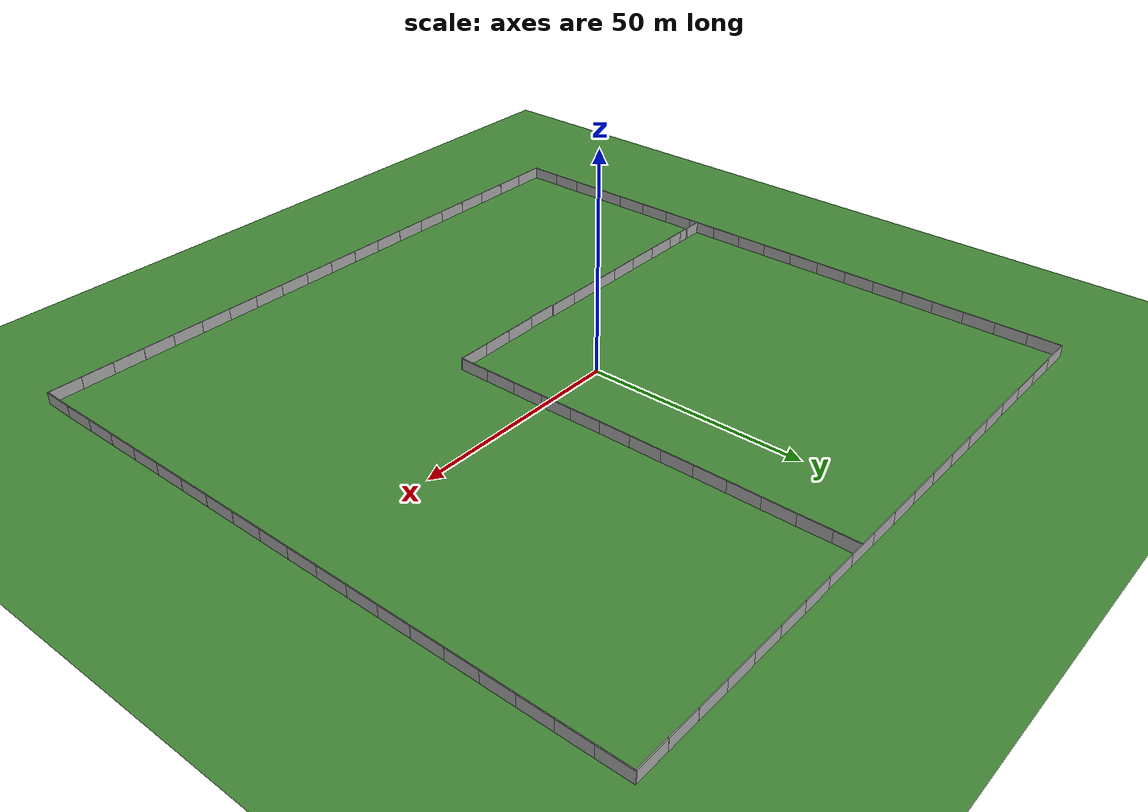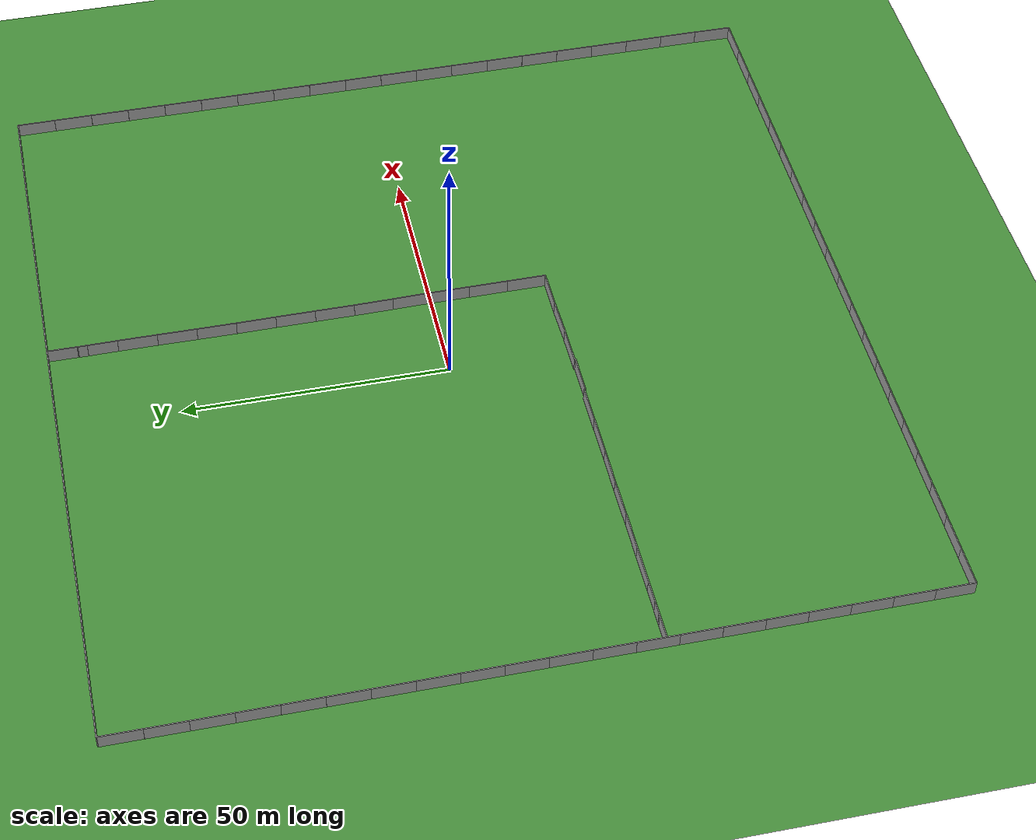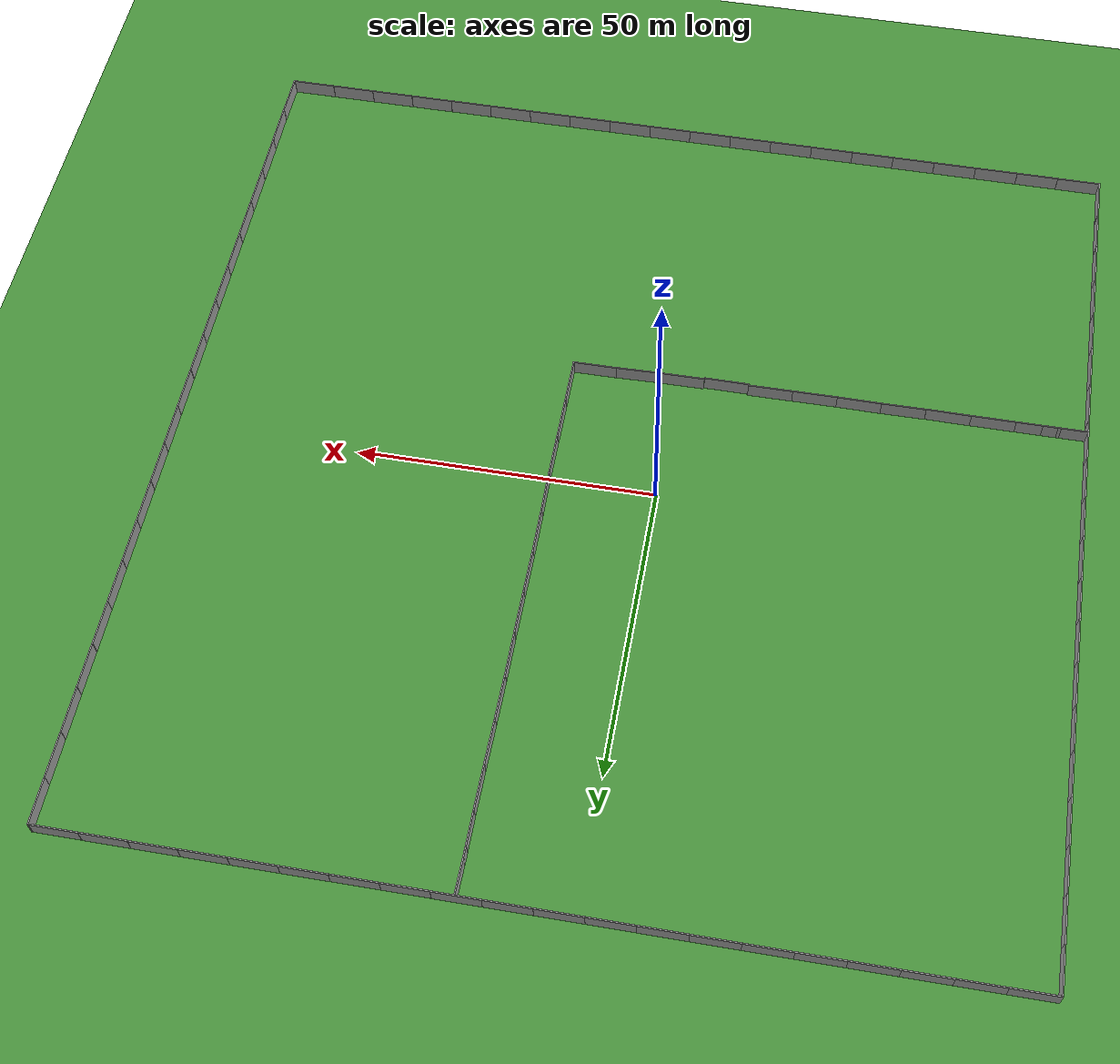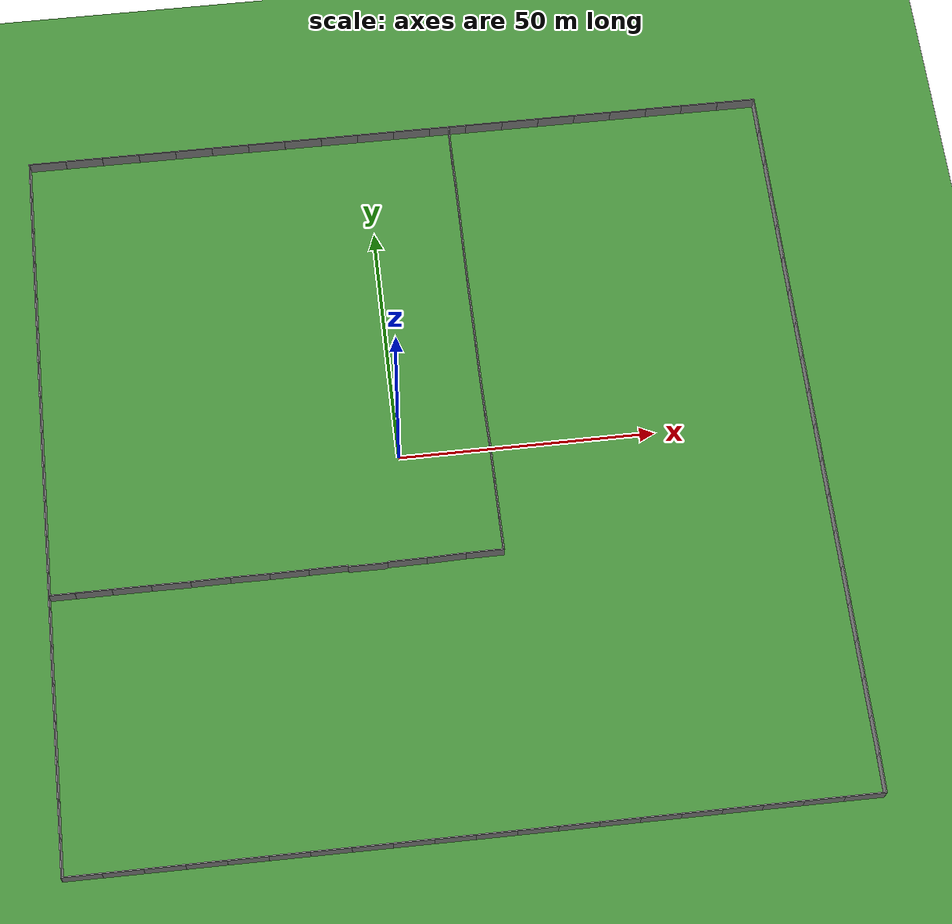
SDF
<sdf version="1.7">
 <world name="default">
  <light name="sun" type="directional">
   <pose>0 0 10 0 -0 0</pose>
   <diffuse>0.8 0.8 0.8 1</diffuse>
   <specular>0.2 0.2 0.2 1</specular>
   <attenuation>
    <range>1000</range>
    <constant>0.9</constant>
    <linear>0.01</linear>
    <quadratic>0.001</quadratic>
   </attenuation>
   <direction>-0.5 0.1 -0.9</direction>
   <spot><inner_angle>0</inner_angle><outer_angle>0</outer_angle><falloff>0</falloff></spot>
  </light>
  <gravity>0 0 -9.8</gravity>
  <magnetic_field>6e-06 2.3e-05 -4.2e-05</magnetic_field>
  <atmosphere type="adiabatic"/>
  <physics name="default_physics" default="0" type="ode">
   <max_step_size>0.001</max_step_size>
   <real_time_factor>1</real_time_factor>
   <real_time_update_rate>1000</real_time_update_rate>
  </physics>
  <scene><ambient>0.4 0.4 0.4 1</ambient><background>0.7 0.7 0.7 1</background><shadows>1</shadows></scene>
  <spherical_coordinates>
   <surface_model>EARTH_WGS84</surface_model>
   <latitude_deg>0</latitude_deg>
   <longitude_deg>0</longitude_deg>
   <elevation>0</elevation>
   <heading_deg>0</heading_deg>
  </spherical_coordinates>
  <model name="vrc_driving_terrain">
   <static>1</static>
   <link name="grass_plane">
    <collision name="collision">
     <geometry><plane><normal>0 0 1</normal><size>150 150</size></plane></geometry>
     <surface><friction><ode><mu>0.5</mu><mu2>0.5</mu2></ode></friction></surface>
    </collision>
    <visual name="visual_0">
     <cast_shadows>0</cast_shadows>
     <geometry><plane><normal>0 0 1</normal><size>150 150</size></plane></geometry>
     <material>
      <script>
       <uri>model://forest/vrc_driving_terrain/materials/scripts</uri>
       <uri>model://forest/vrc_driving_terrain/materials/textures</uri>
       <name>vrc/grass</name>
      </script>
     </material>
    </visual>
   </link>
   <pose>6.27224 -2.36963 0 0 -0 0</pose>
  </model>
  <model name="grey_wall_clone_10_clone_clone_clone_11_clone">
   <static>1</static>
   <link name="link">
    <pose>0 0 1.4 0 -0 0</pose>
    <collision name="collision"><geometry><box><size>7.5 0.2 2.8</size></box></geometry></collision>
    <visual name="visual">
     <cast_shadows>0</cast_shadows>
     <geometry><box><size>7.5 0.2 2.8</size></box></geometry>
     <material>
      <script>
       <uri>model://forest/grey_wall/materials/scripts</uri>
       <uri>model://forest/grey_wall/materials/textures</uri>
       <name>vrc/grey_wall</name>
      </script>
     </material>
    </visual>
   </link>
   <pose>-64.823 -77.1867 0 0 -0 0</pose>
  </model>
  <model name="grey_wall_clone_10_clone_clone_clone_11_clone_clone">
   <static>1</static>
   <link name="link">
    <pose>0 0 1.4 0 -0 0</pose>
    <collision name="collision"><geometry><box><size>7.5 0.2 2.8</size></box></geometry></collision>
    <visual name="visual">
     <cast_shadows>0</cast_shadows>
     <geometry><box><size>7.5 0.2 2.8</size></box></geometry>
     <material>
      <script>
       <uri>model://forest/grey_wall/materials/scripts</uri>
       <uri>model://forest/grey_wall/materials/textures</uri>
       <name>vrc/grey_wall</name>
      </script>
     </material>
    </visual>
   </link>
   <pose>-57.5346 -77.2024 0 0 -0 0</pose>
  </model>
  <model name="grey_wall_clone_10_clone_clone_clone_11_clone_clone_0">
   <static>1</static>
   <link name="link">
    <pose>0 0 1.4 0 -0 0</pose>
    <collision name="collision"><geometry><box><size>7.5 0.2 2.8</size></box></geometry></collision>
    <visual name="visual">
     <cast_shadows>0</cast_shadows>
     <geometry><box><size>7.5 0.2 2.8</size></box></geometry>
     <material>
      <script>
       <uri>model://forest/grey_wall/materials/scripts</uri>
       <uri>model://forest/grey_wall/materials/textures</uri>
       <name>vrc/grey_wall</name>
      </script>
     </material>
    </visual>
   </link>
   <pose>-50.026 -77.2083 0 0 -0 0</pose>
  </model>
  <model name="grey_wall_clone_10_clone_clone_clone_11_clone_clone_1">
   <static>1</static>
   <link name="link">
    <pose>0 0 1.4 0 -0 0</pose>
    <collision name="collision"><geometry><box><size>7.5 0.2 2.8</size></box></geometry></collision>
    <visual name="visual">
     <cast_shadows>0</cast_shadows>
     <geometry><box><size>7.5 0.2 2.8</size></box></geometry>
     <material>
      <script>
       <uri>model://forest/grey_wall/materials/scripts</uri>
       <uri>model://forest/grey_wall/materials/textures</uri>
       <name>vrc/grey_wall</name>
      </script>
     </material>
    </visual>
   </link>
   <pose>-42.5276 -77.1982 0 0 -0 0</pose>
  </model>
  <model name="grey_wall_clone_10_clone_clone_clone_11_clone_clone_2">
   <static>1</static>
   <link name="link">
    <pose>0 0 1.4 0 -0 0</pose>
    <collision name="collision"><geometry><box><size>7.5 0.2 2.8</size></box></geometry></collision>
    <visual name="visual">
     <cast_shadows>0</cast_shadows>
     <geometry><box><size>7.5 0.2 2.8</size></box></geometry>
     <material>
      <script>
       <uri>model://forest/grey_wall/materials/scripts</uri>
       <uri>model://forest/grey_wall/materials/textures</uri>
       <name>vrc/grey_wall</name>
      </script>
     </material>
    </visual>
   </link>
   <pose>-35.0175 -77.2078 0 0 -0 0</pose>
  </model>
  <model name="grey_wall_clone_10_clone_clone_clone_11_clone_clone_3">
   <static>1</static>
   <link name="link">
    <pose>0 0 1.4 0 -0 0</pose>
    <collision name="collision"><geometry><box><size>7.5 0.2 2.8</size></box></geometry></collision>
    <visual name="visual">
     <cast_shadows>0</cast_shadows>
     <geometry><box><size>7.5 0.2 2.8</size></box></geometry>
     <material>
      <script>
       <uri>model://forest/grey_wall/materials/scripts</uri>
       <uri>model://forest/grey_wall/materials/textures</uri>
       <name>vrc/grey_wall</name>
      </script>
     </material>
    </visual>
   </link>
   <pose>-27.5544 -77.2087 0 0 -0 0</pose>
  </model>
  <model name="grey_wall_clone_10_clone_clone_clone_11_clone_clone_4">
   <static>1</static>
   <link name="link">
    <pose>0 0 1.4 0 -0 0</pose>
    <collision name="collision"><geometry><box><size>7.5 0.2 2.8</size></box></geometry></collision>
    <visual name="visual">
     <cast_shadows>0</cast_shadows>
     <geometry><box><size>7.5 0.2 2.8</size></box></geometry>
     <material>
      <script>
       <uri>model://forest/grey_wall/materials/scripts</uri>
       <uri>model://forest/grey_wall/materials/textures</uri>
       <name>vrc/grey_wall</name>
      </script>
     </material>
    </visual>
   </link>
   <pose>-20.0557 -77.2142 0 0 -0 0</pose>
  </model>
  <model name="grey_wall_clone_10_clone_clone_clone_11_clone_clone_5">
   <static>1</static>
   <link name="link">
    <pose>0 0 1.4 0 -0 0</pose>
    <collision name="collision"><geometry><box><size>7.5 0.2 2.8</size></box></geometry></collision>
    <visual name="visual">
     <cast_shadows>0</cast_shadows>
     <geometry><box><size>7.5 0.2 2.8</size></box></geometry>
     <material>
      <script>
       <uri>model://forest/grey_wall/materials/scripts</uri>
       <uri>model://forest/grey_wall/materials/textures</uri>
       <name>vrc/grey_wall</name>
      </script>
     </material>
    </visual>
   </link>
   <pose>-12.5467 -77.224 0 0 -0 0</pose>
  </model>
  <model name="grey_wall_clone_10_clone_clone_clone_11_clone_clone_6">
   <static>1</static>
   <link name="link">
    <pose>0 0 1.4 0 -0 0</pose>
    <collision name="collision"><geometry><box><size>7.5 0.2 2.8</size></box></geometry></collision>
    <visual name="visual">
     <cast_shadows>0</cast_shadows>
     <geometry><box><size>7.5 0.2 2.8</size></box></geometry>
     <material>
      <script>
       <uri>model://forest/grey_wall/materials/scripts</uri>
       <uri>model://forest/grey_wall/materials/textures</uri>
       <name>vrc/grey_wall</name>
      </script>
     </material>
    </visual>
   </link>
   <pose>-5.04952 -77.2253 0 0 -0 0</pose>
  </model>
  <model name="grey_wall_clone_10_clone_clone_clone_11_clone_clone_7">
   <static>1</static>
   <link name="link">
    <pose>0 0 1.4 0 -0 0</pose>
    <collision name="collision"><geometry><box><size>7.5 0.2 2.8</size></box></geometry></collision>
    <visual name="visual">
     <cast_shadows>0</cast_shadows>
     <geometry><box><size>7.5 0.2 2.8</size></box></geometry>
     <material>
      <script>
       <uri>model://forest/grey_wall/materials/scripts</uri>
       <uri>model://forest/grey_wall/materials/textures</uri>
       <name>vrc/grey_wall</name>
      </script>
     </material>
    </visual>
   </link>
   <pose>2.45064 -77.2385 0 0 -0 0</pose>
  </model>
  <model name="grey_wall_clone_10_clone_clone_clone_11_clone_clone_8">
   <static>1</static>
   <link name="link">
    <pose>0 0 1.4 0 -0 0</pose>
    <collision name="collision"><geometry><box><size>7.5 0.2 2.8</size></box></geometry></collision>
    <visual name="visual">
     <cast_shadows>0</cast_shadows>
     <geometry><box><size>7.5 0.2 2.8</size></box></geometry>
     <material>
      <script>
       <uri>model://forest/grey_wall/materials/scripts</uri>
       <uri>model://forest/grey_wall/materials/textures</uri>
       <name>vrc/grey_wall</name>
      </script>
     </material>
    </visual>
   </link>
   <pose>9.9578 -77.2456 0 0 -0 0</pose>
  </model>
  <model name="grey_wall_clone_10_clone_clone_clone_11_clone_clone_9">
   <static>1</static>
   <link name="link">
    <pose>0 0 1.4 0 -0 0</pose>
    <collision name="collision"><geometry><box><size>7.5 0.2 2.8</size></box></geometry></collision>
    <visual name="visual">
     <cast_shadows>0</cast_shadows>
     <geometry><box><size>7.5 0.2 2.8</size></box></geometry>
     <material>
      <script>
       <uri>model://forest/grey_wall/materials/scripts</uri>
       <uri>model://forest/grey_wall/materials/textures</uri>
       <name>vrc/grey_wall</name>
      </script>
     </material>
    </visual>
   </link>
   <pose>17.442 -77.2428 0 0 -0 0</pose>
  </model>
  <model name="grey_wall_clone_10_clone_clone_clone_11_clone_clone_10">
   <static>1</static>
   <link name="link">
    <pose>0 0 1.4 0 -0 0</pose>
    <collision name="collision"><geometry><box><size>7.5 0.2 2.8</size></box></geometry></collision>
    <visual name="visual">
     <cast_shadows>0</cast_shadows>
     <geometry><box><size>7.5 0.2 2.8</size></box></geometry>
     <material>
      <script>
       <uri>model://forest/grey_wall/materials/scripts</uri>
       <uri>model://forest/grey_wall/materials/textures</uri>
       <name>vrc/grey_wall</name>
      </script>
     </material>
    </visual>
   </link>
   <pose>24.9441 -77.2473 0 0 -0 0</pose>
  </model>
  <model name="grey_wall_clone_10_clone_clone_clone_11_clone_clone_11">
   <static>1</static>
   <link name="link">
    <pose>0 0 1.4 0 -0 0</pose>
    <collision name="collision"><geometry><box><size>7.5 0.2 2.8</size></box></geometry></collision>
    <visual name="visual">
     <cast_shadows>0</cast_shadows>
     <geometry><box><size>7.5 0.2 2.8</size></box></geometry>
     <material>
      <script>
       <uri>model://forest/grey_wall/materials/scripts</uri>
       <uri>model://forest/grey_wall/materials/textures</uri>
       <name>vrc/grey_wall</name>
      </script>
     </material>
    </visual>
   </link>
   <pose>32.4421 -77.2463 0 0 -0 0</pose>
  </model>
  <model name="grey_wall_clone_10_clone_clone_clone_11_clone_clone_12">
   <static>1</static>
   <link name="link">
    <pose>0 0 1.4 0 -0 0</pose>
    <collision name="collision"><geometry><box><size>7.5 0.2 2.8</size></box></geometry></collision>
    <visual name="visual">
     <cast_shadows>0</cast_shadows>
     <geometry><box><size>7.5 0.2 2.8</size></box></geometry>
     <material>
      <script>
       <uri>model://forest/grey_wall/materials/scripts</uri>
       <uri>model://forest/grey_wall/materials/textures</uri>
       <name>vrc/grey_wall</name>
      </script>
     </material>
    </visual>
   </link>
   <pose>39.9314 -77.2456 0 0 -0 0</pose>
  </model>
  <model name="grey_wall_clone_10_clone_clone_clone_11_clone_clone_13">
   <static>1</static>
   <link name="link">
    <pose>0 0 1.4 0 -0 0</pose>
    <collision name="collision"><geometry><box><size>7.5 0.2 2.8</size></box></geometry></collision>
    <visual name="visual">
     <cast_shadows>0</cast_shadows>
     <geometry><box><size>7.5 0.2 2.8</size></box></geometry>
     <material>
      <script>
       <uri>model://forest/grey_wall/materials/scripts</uri>
       <uri>model://forest/grey_wall/materials/textures</uri>
       <name>vrc/grey_wall</name>
      </script>
     </material>
    </visual>
   </link>
   <pose>47.429 -77.2489 0 0 -0 0</pose>
  </model>
  <model name="grey_wall_clone_10_clone_clone_clone_11_clone_clone_14">
   <static>1</static>
   <link name="link">
    <pose>0 0 1.4 0 -0 0</pose>
    <collision name="collision"><geometry><box><size>7.5 0.2 2.8</size></box></geometry></collision>
    <visual name="visual">
     <cast_shadows>0</cast_shadows>
     <geometry><box><size>7.5 0.2 2.8</size></box></geometry>
     <material>
      <script>
       <uri>model://forest/grey_wall/materials/scripts</uri>
       <uri>model://forest/grey_wall/materials/textures</uri>
       <name>vrc/grey_wall</name>
      </script>
     </material>
    </visual>
   </link>
   <pose>54.8935 -77.2438 0 0 -0 0</pose>
  </model>
  <model name="grey_wall_clone_10_clone_clone_clone_11_clone_clone_15">
   <static>1</static>
   <link name="link">
    <pose>0 0 1.4 0 -0 0</pose>
    <collision name="collision"><geometry><box><size>7.5 0.2 2.8</size></box></geometry></collision>
    <visual name="visual">
     <cast_shadows>0</cast_shadows>
     <geometry><box><size>7.5 0.2 2.8</size></box></geometry>
     <material>
      <script>
       <uri>model://forest/grey_wall/materials/scripts</uri>
       <uri>model://forest/grey_wall/materials/textures</uri>
       <name>vrc/grey_wall</name>
      </script>
     </material>
    </visual>
   </link>
   <pose>62.4043 -77.2429 0 0 -0 0</pose>
  </model>
  <model name="grey_wall_clone_10_clone_clone_clone_11_clone_clone_16">
   <static>1</static>
   <link name="link">
    <pose>0 0 1.4 0 -0 0</pose>
    <collision name="collision"><geometry><box><size>7.5 0.2 2.8</size></box></geometry></collision>
    <visual name="visual">
     <cast_shadows>0</cast_shadows>
     <geometry><box><size>7.5 0.2 2.8</size></box></geometry>
     <material>
      <script>
       <uri>model://forest/grey_wall/materials/scripts</uri>
       <uri>model://forest/grey_wall/materials/textures</uri>
       <name>vrc/grey_wall</name>
      </script>
     </material>
    </visual>
   </link>
   <pose>69.8968 -77.2494 0 0 -0 0</pose>
  </model>
  <model name="grey_wall_clone_10_clone_clone_clone_11_clone_clone_17">
   <static>1</static>
   <link name="link">
    <pose>0 0 1.4 0 -0 0</pose>
    <collision name="collision"><geometry><box><size>7.5 0.2 2.8</size></box></geometry></collision>
    <visual name="visual">
     <cast_shadows>0</cast_shadows>
     <geometry><box><size>7.5 0.2 2.8</size></box></geometry>
     <material>
      <script>
       <uri>model://forest/grey_wall/materials/scripts</uri>
       <uri>model://forest/grey_wall/materials/textures</uri>
       <name>vrc/grey_wall</name>
      </script>
     </material>
    </visual>
   </link>
   <pose>77.4066 -77.2521 0 0 -0 0</pose>
  </model>
  <model name="grey_wall_clone_10_clone_0_clone_11_clone">
   <static>1</static>
   <link name="link">
    <pose>0 0 1.4 0 -0 0</pose>
    <collision name="collision"><geometry><box><size>7.5 0.2 2.8</size></box></geometry></collision>
    <visual name="visual">
     <cast_shadows>0</cast_shadows>
     <geometry><box><size>7.5 0.2 2.8</size></box></geometry>
     <material>
      <script>
       <uri>model://forest/grey_wall/materials/scripts</uri>
       <uri>model://forest/grey_wall/materials/textures</uri>
       <name>vrc/grey_wall</name>
      </script>
     </material>
    </visual>
   </link>
   <pose>81.2442 -73.5802 0 0 0 -1.5802</pose>
  </model>
  <model name="grey_wall_clone_10_clone_0_clone_10_clone">
   <static>1</static>
   <link name="link">
    <pose>0 0 1.4 0 -0 0</pose>
    <collision name="collision"><geometry><box><size>7.5 0.2 2.8</size></box></geometry></collision>
    <visual name="visual">
     <cast_shadows>0</cast_shadows>
     <geometry><box><size>7.5 0.2 2.8</size></box></geometry>
     <material>
      <script>
       <uri>model://forest/grey_wall/materials/scripts</uri>
       <uri>model://forest/grey_wall/materials/textures</uri>
       <name>vrc/grey_wall</name>
      </script>
     </material>
    </visual>
   </link>
   <pose>81.3001 -66.0858 0 0 0 -1.56932</pose>
  </model>
  <model name="grey_wall_clone_10_clone_0_clone_9_clone">
   <static>1</static>
   <link name="link">
    <pose>0 0 1.4 0 -0 0</pose>
    <collision name="collision"><geometry><box><size>7.5 0.2 2.8</size></box></geometry></collision>
    <visual name="visual">
     <cast_shadows>0</cast_shadows>
     <geometry><box><size>7.5 0.2 2.8</size></box></geometry>
     <material>
      <script>
       <uri>model://forest/grey_wall/materials/scripts</uri>
       <uri>model://forest/grey_wall/materials/textures</uri>
       <name>vrc/grey_wall</name>
      </script>
     </material>
    </visual>
   </link>
   <pose>81.2777 -58.6142 0 0 0 -1.56932</pose>
  </model>
  <model name="grey_wall_clone_10_clone_0_clone_8_clone">
   <static>1</static>
   <link name="link">
    <pose>0 0 1.4 0 -0 0</pose>
    <collision name="collision"><geometry><box><size>7.5 0.2 2.8</size></box></geometry></collision>
    <visual name="visual">
     <cast_shadows>0</cast_shadows>
     <geometry><box><size>7.5 0.2 2.8</size></box></geometry>
     <material>
      <script>
       <uri>model://forest/grey_wall/materials/scripts</uri>
       <uri>model://forest/grey_wall/materials/textures</uri>
       <name>vrc/grey_wall</name>
      </script>
     </material>
    </visual>
   </link>
   <pose>81.2777 -51.1177 0 0 0 -1.56932</pose>
  </model>
  <model name="grey_wall_clone_10_clone_0_clone_7_clone">
   <static>1</static>
   <link name="link">
    <pose>0 0 1.4 0 -0 0</pose>
    <collision name="collision"><geometry><box><size>7.5 0.2 2.8</size></box></geometry></collision>
    <visual name="visual">
     <cast_shadows>0</cast_shadows>
     <geometry><box><size>7.5 0.2 2.8</size></box></geometry>
     <material>
      <script>
       <uri>model://forest/grey_wall/materials/scripts</uri>
       <uri>model://forest/grey_wall/materials/textures</uri>
       <name>vrc/grey_wall</name>
      </script>
     </material>
    </visual>
   </link>
   <pose>81.2788 -43.6064 0 0 0 -1.56932</pose>
  </model>
  <model name="grey_wall_clone_10_clone_0_clone_6_clone">
   <static>1</static>
   <link name="link">
    <pose>0 0 1.4 0 -0 0</pose>
    <collision name="collision"><geometry><box><size>7.5 0.2 2.8</size></box></geometry></collision>
    <visual name="visual">
     <cast_shadows>0</cast_shadows>
     <geometry><box><size>7.5 0.2 2.8</size></box></geometry>
     <material>
      <script>
       <uri>model://forest/grey_wall/materials/scripts</uri>
       <uri>model://forest/grey_wall/materials/textures</uri>
       <name>vrc/grey_wall</name>
      </script>
     </material>
    </visual>
   </link>
   <pose>81.2767 -36.0958 0 0 0 -1.56932</pose>
  </model>
  <model name="grey_wall_clone_10_clone_0_clone_5_clone_13">
   <static>1</static>
   <link name="link">
    <pose>0 0 1.4 0 -0 0</pose>
    <collision name="collision"><geometry><box><size>7.5 0.2 2.8</size></box></geometry></collision>
    <visual name="visual">
     <cast_shadows>0</cast_shadows>
     <geometry><box><size>7.5 0.2 2.8</size></box></geometry>
     <material>
      <script>
       <uri>model://forest/grey_wall/materials/scripts</uri>
       <uri>model://forest/grey_wall/materials/textures</uri>
       <name>vrc/grey_wall</name>
      </script>
     </material>
    </visual>
   </link>
   <pose>81.2728 -28.5811 0 0 0 -1.56932</pose>
  </model>
  <model name="grey_wall_clone_10_clone_0_clone_4_clone">
   <static>1</static>
   <link name="link">
    <pose>0 0 1.4 0 -0 0</pose>
    <collision name="collision"><geometry><box><size>7.5 0.2 2.8</size></box></geometry></collision>
    <visual name="visual">
     <cast_shadows>0</cast_shadows>
     <geometry><box><size>7.5 0.2 2.8</size></box></geometry>
     <material>
      <script>
       <uri>model://forest/grey_wall/materials/scripts</uri>
       <uri>model://forest/grey_wall/materials/textures</uri>
       <name>vrc/grey_wall</name>
      </script>
     </material>
    </visual>
   </link>
   <pose>81.2736 -21.0806 0 0 0 -1.56932</pose>
  </model>
  <model name="grey_wall_clone_10_clone_0_clone_3_clone">
   <static>1</static>
   <link name="link">
    <pose>0 0 1.4 0 -0 0</pose>
    <collision name="collision"><geometry><box><size>7.5 0.2 2.8</size></box></geometry></collision>
    <visual name="visual">
     <cast_shadows>0</cast_shadows>
     <geometry><box><size>7.5 0.2 2.8</size></box></geometry>
     <material>
      <script>
       <uri>model://forest/grey_wall/materials/scripts</uri>
       <uri>model://forest/grey_wall/materials/textures</uri>
       <name>vrc/grey_wall</name>
      </script>
     </material>
    </visual>
   </link>
   <pose>81.2554 -13.5842 0 0 0 -1.56932</pose>
  </model>
  <model name="grey_wall_clone_10_clone_0_clone_2_clone">
   <static>1</static>
   <link name="link">
    <pose>0 0 1.4 0 -0 0</pose>
    <collision name="collision"><geometry><box><size>7.5 0.2 2.8</size></box></geometry></collision>
    <visual name="visual">
     <cast_shadows>0</cast_shadows>
     <geometry><box><size>7.5 0.2 2.8</size></box></geometry>
     <material>
      <script>
       <uri>model://forest/grey_wall/materials/scripts</uri>
       <uri>model://forest/grey_wall/materials/textures</uri>
       <name>vrc/grey_wall</name>
      </script>
     </material>
    </visual>
   </link>
   <pose>81.262 -6.06923 0 0 0 -1.56932</pose>
  </model>
  <model name="grey_wall_clone_10_clone_0_clone_1_clone">
   <static>1</static>
   <link name="link">
    <pose>0 0 1.4 0 -0 0</pose>
    <collision name="collision"><geometry><box><size>7.5 0.2 2.8</size></box></geometry></collision>
    <visual name="visual">
     <cast_shadows>0</cast_shadows>
     <geometry><box><size>7.5 0.2 2.8</size></box></geometry>
     <material>
      <script>
       <uri>model://forest/grey_wall/materials/scripts</uri>
       <uri>model://forest/grey_wall/materials/textures</uri>
       <name>vrc/grey_wall</name>
      </script>
     </material>
    </visual>
   </link>
   <pose>81.2538 1.43804 0 0 0 -1.56932</pose>
  </model>
  <model name="grey_wall_clone_10_clone_0_clone_0_clone">
   <static>1</static>
   <link name="link">
    <pose>0 0 1.4 0 -0 0</pose>
    <collision name="collision"><geometry><box><size>7.5 0.2 2.8</size></box></geometry></collision>
    <visual name="visual">
     <cast_shadows>0</cast_shadows>
     <geometry><box><size>7.5 0.2 2.8</size></box></geometry>
     <material>
      <script>
       <uri>model://forest/grey_wall/materials/scripts</uri>
       <uri>model://forest/grey_wall/materials/textures</uri>
       <name>vrc/grey_wall</name>
      </script>
     </material>
    </visual>
   </link>
   <pose>81.2487 8.94341 0 0 0 -1.56932</pose>
  </model>
  <model name="grey_wall_clone_10_clone_0_clone_clone">
   <static>1</static>
   <link name="link">
    <pose>0 0 1.4 0 -0 0</pose>
    <collision name="collision"><geometry><box><size>7.5 0.2 2.8</size></box></geometry></collision>
    <visual name="visual">
     <cast_shadows>0</cast_shadows>
     <geometry><box><size>7.5 0.2 2.8</size></box></geometry>
     <material>
      <script>
       <uri>model://forest/grey_wall/materials/scripts</uri>
       <uri>model://forest/grey_wall/materials/textures</uri>
       <name>vrc/grey_wall</name>
      </script>
     </material>
    </visual>
   </link>
   <pose>81.244 16.4592 0 0 0 -1.56932</pose>
  </model>
  <model name="grey_wall_clone_10_clone_0_clone_12">
   <static>1</static>
   <link name="link">
    <pose>0 0 1.4 0 -0 0</pose>
    <collision name="collision"><geometry><box><size>7.5 0.2 2.8</size></box></geometry></collision>
    <visual name="visual">
     <cast_shadows>0</cast_shadows>
     <geometry><box><size>7.5 0.2 2.8</size></box></geometry>
     <material>
      <script>
       <uri>model://forest/grey_wall/materials/scripts</uri>
       <uri>model://forest/grey_wall/materials/textures</uri>
       <name>vrc/grey_wall</name>
      </script>
     </material>
    </visual>
   </link>
   <pose>81.241 23.9604 0 0 0 -1.56932</pose>
  </model>
  <model name="grey_wall_clone_10_clone_0_clone_13">
   <static>1</static>
   <link name="link">
    <pose>0 0 1.4 0 -0 0</pose>
    <collision name="collision"><geometry><box><size>7.5 0.2 2.8</size></box></geometry></collision>
    <visual name="visual">
     <cast_shadows>0</cast_shadows>
     <geometry><box><size>7.5 0.2 2.8</size></box></geometry>
     <material>
      <script>
       <uri>model://forest/grey_wall/materials/scripts</uri>
       <uri>model://forest/grey_wall/materials/textures</uri>
       <name>vrc/grey_wall</name>
      </script>
     </material>
    </visual>
   </link>
   <pose>81.233 31.4667 0 0 0 -1.56932</pose>
  </model>
  <model name="grey_wall_clone_10_clone_0_clone_14">
   <static>1</static>
   <link name="link">
    <pose>0 0 1.4 0 -0 0</pose>
    <collision name="collision"><geometry><box><size>7.5 0.2 2.8</size></box></geometry></collision>
    <visual name="visual">
     <cast_shadows>0</cast_shadows>
     <geometry><box><size>7.5 0.2 2.8</size></box></geometry>
     <material>
      <script>
       <uri>model://forest/grey_wall/materials/scripts</uri>
       <uri>model://forest/grey_wall/materials/textures</uri>
       <name>vrc/grey_wall</name>
      </script>
     </material>
    </visual>
   </link>
   <pose>81.2299 38.978 0 0 0 -1.56932</pose>
  </model>
  <model name="grey_wall_clone_10_clone_0_clone_15">
   <static>1</static>
   <link name="link">
    <pose>0 0 1.4 0 -0 0</pose>
    <collision name="collision"><geometry><box><size>7.5 0.2 2.8</size></box></geometry></collision>
    <visual name="visual">
     <cast_shadows>0</cast_shadows>
     <geometry><box><size>7.5 0.2 2.8</size></box></geometry>
     <material>
      <script>
       <uri>model://forest/grey_wall/materials/scripts</uri>
       <uri>model://forest/grey_wall/materials/textures</uri>
       <name>vrc/grey_wall</name>
      </script>
     </material>
    </visual>
   </link>
   <pose>81.2399 46.4861 0 0 0 -1.56932</pose>
  </model>
  <model name="grey_wall_clone_10_clone_0_clone_16">
   <static>1</static>
   <link name="link">
    <pose>0 0 1.4 0 -0 0</pose>
    <collision name="collision"><geometry><box><size>7.5 0.2 2.8</size></box></geometry></collision>
    <visual name="visual">
     <cast_shadows>0</cast_shadows>
     <geometry><box><size>7.5 0.2 2.8</size></box></geometry>
     <material>
      <script>
       <uri>model://forest/grey_wall/materials/scripts</uri>
       <uri>model://forest/grey_wall/materials/textures</uri>
       <name>vrc/grey_wall</name>
      </script>
     </material>
    </visual>
   </link>
   <pose>81.2341 53.9889 0 0 0 -1.56932</pose>
  </model>
  <model name="grey_wall_clone_10_clone_0_clone_17">
   <static>1</static>
   <link name="link">
    <pose>0 0 1.4 0 -0 0</pose>
    <collision name="collision"><geometry><box><size>7.5 0.2 2.8</size></box></geometry></collision>
    <visual name="visual">
     <cast_shadows>0</cast_shadows>
     <geometry><box><size>7.5 0.2 2.8</size></box></geometry>
     <material>
      <script>
       <uri>model://forest/grey_wall/materials/scripts</uri>
       <uri>model://forest/grey_wall/materials/textures</uri>
       <name>vrc/grey_wall</name>
      </script>
     </material>
    </visual>
   </link>
   <pose>81.2319 61.4946 0 0 0 -1.56932</pose>
  </model>
  <model name="grey_wall_clone_10_clone_0_clone_18">
   <static>1</static>
   <link name="link">
    <pose>0 0 1.4 0 -0 0</pose>
    <collision name="collision"><geometry><box><size>7.5 0.2 2.8</size></box></geometry></collision>
    <visual name="visual">
     <cast_shadows>0</cast_shadows>
     <geometry><box><size>7.5 0.2 2.8</size></box></geometry>
     <material>
      <script>
       <uri>model://forest/grey_wall/materials/scripts</uri>
       <uri>model://forest/grey_wall/materials/textures</uri>
       <name>vrc/grey_wall</name>
      </script>
     </material>
    </visual>
   </link>
   <pose>81.2148 68.9647 0 0 0 -1.56932</pose>
  </model>
  <model name="grey_wall_clone_10_clone_clone_0">
   <static>1</static>
   <link name="link">
    <pose>0 0 1.4 0 -0 0</pose>
    <collision name="collision"><geometry><box><size>7.5 0.2 2.8</size></box></geometry></collision>
    <visual name="visual">
     <cast_shadows>0</cast_shadows>
     <geometry><box><size>7.5 0.2 2.8</size></box></geometry>
     <material>
      <script>
       <uri>model://forest/grey_wall/materials/scripts</uri>
       <uri>model://forest/grey_wall/materials/textures</uri>
       <name>vrc/grey_wall</name>
      </script>
     </material>
    </visual>
   </link>
   <pose>77.3508 72.6116 0 0 -0 0</pose>
  </model>
  <model name="grey_wall_clone_10_clone_clone_1">
   <static>1</static>
   <link name="link">
    <pose>0 0 1.4 0 -0 0</pose>
    <collision name="collision"><geometry><box><size>7.5 0.2 2.8</size></box></geometry></collision>
    <visual name="visual">
     <cast_shadows>0</cast_shadows>
     <geometry><box><size>7.5 0.2 2.8</size></box></geometry>
     <material>
      <script>
       <uri>model://forest/grey_wall/materials/scripts</uri>
       <uri>model://forest/grey_wall/materials/textures</uri>
       <name>vrc/grey_wall</name>
      </script>
     </material>
    </visual>
   </link>
   <pose>69.8438 72.6289 0 0 -0 0</pose>
  </model>
  <model name="grey_wall_clone_10_clone_clone_2">
   <static>1</static>
   <link name="link">
    <pose>0 0 1.4 0 -0 0</pose>
    <collision name="collision"><geometry><box><size>7.5 0.2 2.8</size></box></geometry></collision>
    <visual name="visual">
     <cast_shadows>0</cast_shadows>
     <geometry><box><size>7.5 0.2 2.8</size></box></geometry>
     <material>
      <script>
       <uri>model://forest/grey_wall/materials/scripts</uri>
       <uri>model://forest/grey_wall/materials/textures</uri>
       <name>vrc/grey_wall</name>
      </script>
     </material>
    </visual>
   </link>
   <pose>62.3519 72.6417 0 0 -0 0</pose>
  </model>
  <model name="grey_wall_clone_10_clone_clone_3">
   <static>1</static>
   <link name="link">
    <pose>0 0 1.4 0 -0 0</pose>
    <collision name="collision"><geometry><box><size>7.5 0.2 2.8</size></box></geometry></collision>
    <visual name="visual">
     <cast_shadows>0</cast_shadows>
     <geometry><box><size>7.5 0.2 2.8</size></box></geometry>
     <material>
      <script>
       <uri>model://forest/grey_wall/materials/scripts</uri>
       <uri>model://forest/grey_wall/materials/textures</uri>
       <name>vrc/grey_wall</name>
      </script>
     </material>
    </visual>
   </link>
   <pose>54.875 72.6299 0 0 -0 0</pose>
  </model>
  <model name="grey_wall_clone_10_clone_clone_4">
   <static>1</static>
   <link name="link">
    <pose>0 0 1.4 0 -0 0</pose>
    <collision name="collision"><geometry><box><size>7.5 0.2 2.8</size></box></geometry></collision>
    <visual name="visual">
     <cast_shadows>0</cast_shadows>
     <geometry><box><size>7.5 0.2 2.8</size></box></geometry>
     <material>
      <script>
       <uri>model://forest/grey_wall/materials/scripts</uri>
       <uri>model://forest/grey_wall/materials/textures</uri>
       <name>vrc/grey_wall</name>
      </script>
     </material>
    </visual>
   </link>
   <pose>47.3663 72.6324 0 0 -0 0</pose>
  </model>
  <model name="grey_wall_clone_10_clone_clone_5">
   <static>1</static>
   <link name="link">
    <pose>0 0 1.4 0 -0 0</pose>
    <collision name="collision"><geometry><box><size>7.5 0.2 2.8</size></box></geometry></collision>
    <visual name="visual">
     <cast_shadows>0</cast_shadows>
     <geometry><box><size>7.5 0.2 2.8</size></box></geometry>
     <material>
      <script>
       <uri>model://forest/grey_wall/materials/scripts</uri>
       <uri>model://forest/grey_wall/materials/textures</uri>
       <name>vrc/grey_wall</name>
      </script>
     </material>
    </visual>
   </link>
   <pose>39.8774 72.6251 0 0 -0 0</pose>
  </model>
  <model name="grey_wall_clone_10_clone_clone_6">
   <static>1</static>
   <link name="link">
    <pose>0 0 1.4 0 -0 0</pose>
    <collision name="collision"><geometry><box><size>7.5 0.2 2.8</size></box></geometry></collision>
    <visual name="visual">
     <cast_shadows>0</cast_shadows>
     <geometry><box><size>7.5 0.2 2.8</size></box></geometry>
     <material>
      <script>
       <uri>model://forest/grey_wall/materials/scripts</uri>
       <uri>model://forest/grey_wall/materials/textures</uri>
       <name>vrc/grey_wall</name>
      </script>
     </material>
    </visual>
   </link>
   <pose>32.3692 72.6193 0 0 -0 0</pose>
  </model>
  <model name="grey_wall_clone_10_clone_clone_7">
   <static>1</static>
   <link name="link">
    <pose>0 0 1.4 0 -0 0</pose>
    <collision name="collision"><geometry><box><size>7.5 0.2 2.8</size></box></geometry></collision>
    <visual name="visual">
     <cast_shadows>0</cast_shadows>
     <geometry><box><size>7.5 0.2 2.8</size></box></geometry>
     <material>
      <script>
       <uri>model://forest/grey_wall/materials/scripts</uri>
       <uri>model://forest/grey_wall/materials/textures</uri>
       <name>vrc/grey_wall</name>
      </script>
     </material>
    </visual>
   </link>
   <pose>24.8712 72.6187 0 0 -0 0</pose>
  </model>
  <model name="grey_wall_clone_10_clone_clone_8">
   <static>1</static>
   <link name="link">
    <pose>0 0 1.4 0 -0 0</pose>
    <collision name="collision"><geometry><box><size>7.5 0.2 2.8</size></box></geometry></collision>
    <visual name="visual">
     <cast_shadows>0</cast_shadows>
     <geometry><box><size>7.5 0.2 2.8</size></box></geometry>
     <material>
      <script>
       <uri>model://forest/grey_wall/materials/scripts</uri>
       <uri>model://forest/grey_wall/materials/textures</uri>
       <name>vrc/grey_wall</name>
      </script>
     </material>
    </visual>
   </link>
   <pose>17.3775 72.6269 0 0 -0 0</pose>
  </model>
  <model name="grey_wall_clone_10_clone_clone_9">
   <static>1</static>
   <link name="link">
    <pose>0 0 1.4 0 -0 0</pose>
    <collision name="collision"><geometry><box><size>7.5 0.2 2.8</size></box></geometry></collision>
    <visual name="visual">
     <cast_shadows>0</cast_shadows>
     <geometry><box><size>7.5 0.2 2.8</size></box></geometry>
     <material>
      <script>
       <uri>model://forest/grey_wall/materials/scripts</uri>
       <uri>model://forest/grey_wall/materials/textures</uri>
       <name>vrc/grey_wall</name>
      </script>
     </material>
    </visual>
   </link>
   <pose>9.8792 72.6386 0 0 -0 0</pose>
  </model>
  <model name="grey_wall_clone_10_clone_clone_10">
   <static>1</static>
   <link name="link">
    <pose>0 0 1.4 0 -0 0</pose>
    <collision name="collision"><geometry><box><size>7.5 0.2 2.8</size></box></geometry></collision>
    <visual name="visual">
     <cast_shadows>0</cast_shadows>
     <geometry><box><size>7.5 0.2 2.8</size></box></geometry>
     <material>
      <script>
       <uri>model://forest/grey_wall/materials/scripts</uri>
       <uri>model://forest/grey_wall/materials/textures</uri>
       <name>vrc/grey_wall</name>
      </script>
     </material>
    </visual>
   </link>
   <pose>2.37975 72.635 0 0 -0 0</pose>
  </model>
  <model name="grey_wall_clone_10_clone_clone_11">
   <static>1</static>
   <link name="link">
    <pose>0 0 1.4 0 -0 0</pose>
    <collision name="collision"><geometry><box><size>7.5 0.2 2.8</size></box></geometry></collision>
    <visual name="visual">
     <cast_shadows>0</cast_shadows>
     <geometry><box><size>7.5 0.2 2.8</size></box></geometry>
     <material>
      <script>
       <uri>model://forest/grey_wall/materials/scripts</uri>
       <uri>model://forest/grey_wall/materials/textures</uri>
       <name>vrc/grey_wall</name>
      </script>
     </material>
    </visual>
   </link>
   <pose>-5.09788 72.6331 0 0 -0 0</pose>
  </model>
  <model name="grey_wall_clone_10_clone_clone_12">
   <static>1</static>
   <link name="link">
    <pose>0 0 1.4 0 -0 0</pose>
    <collision name="collision"><geometry><box><size>7.5 0.2 2.8</size></box></geometry></collision>
    <visual name="visual">
     <cast_shadows>0</cast_shadows>
     <geometry><box><size>7.5 0.2 2.8</size></box></geometry>
     <material>
      <script>
       <uri>model://forest/grey_wall/materials/scripts</uri>
       <uri>model://forest/grey_wall/materials/textures</uri>
       <name>vrc/grey_wall</name>
      </script>
     </material>
    </visual>
   </link>
   <pose>-12.6061 72.6425 0 0 -0 0</pose>
  </model>
  <model name="grey_wall_clone_10_clone_clone_13">
   <static>1</static>
   <link name="link">
    <pose>0 0 1.4 0 -0 0</pose>
    <collision name="collision"><geometry><box><size>7.5 0.2 2.8</size></box></geometry></collision>
    <visual name="visual">
     <cast_shadows>0</cast_shadows>
     <geometry><box><size>7.5 0.2 2.8</size></box></geometry>
     <material>
      <script>
       <uri>model://forest/grey_wall/materials/scripts</uri>
       <uri>model://forest/grey_wall/materials/textures</uri>
       <name>vrc/grey_wall</name>
      </script>
     </material>
    </visual>
   </link>
   <pose>-20.1193 72.6527 0 0 -0 0</pose>
  </model>
  <model name="grey_wall_clone_10_clone_clone_14">
   <static>1</static>
   <link name="link">
    <pose>0 0 1.4 0 -0 0</pose>
    <collision name="collision"><geometry><box><size>7.5 0.2 2.8</size></box></geometry></collision>
    <visual name="visual">
     <cast_shadows>0</cast_shadows>
     <geometry><box><size>7.5 0.2 2.8</size></box></geometry>
     <material>
      <script>
       <uri>model://forest/grey_wall/materials/scripts</uri>
       <uri>model://forest/grey_wall/materials/textures</uri>
       <name>vrc/grey_wall</name>
      </script>
     </material>
    </visual>
   </link>
   <pose>-27.6199 72.6558 0 0 -0 0</pose>
  </model>
  <model name="grey_wall_clone_10_clone_clone_15">
   <static>1</static>
   <link name="link">
    <pose>0 0 1.4 0 -0 0</pose>
    <collision name="collision"><geometry><box><size>7.5 0.2 2.8</size></box></geometry></collision>
    <visual name="visual">
     <cast_shadows>0</cast_shadows>
     <geometry><box><size>7.5 0.2 2.8</size></box></geometry>
     <material>
      <script>
       <uri>model://forest/grey_wall/materials/scripts</uri>
       <uri>model://forest/grey_wall/materials/textures</uri>
       <name>vrc/grey_wall</name>
      </script>
     </material>
    </visual>
   </link>
   <pose>-35.1125 72.6503 0 0 -0 0</pose>
  </model>
  <model name="grey_wall_clone_10_clone_clone_16">
   <static>1</static>
   <link name="link">
    <pose>0 0 1.4 0 -0 0</pose>
    <collision name="collision"><geometry><box><size>7.5 0.2 2.8</size></box></geometry></collision>
    <visual name="visual">
     <cast_shadows>0</cast_shadows>
     <geometry><box><size>7.5 0.2 2.8</size></box></geometry>
     <material>
      <script>
       <uri>model://forest/grey_wall/materials/scripts</uri>
       <uri>model://forest/grey_wall/materials/textures</uri>
       <name>vrc/grey_wall</name>
      </script>
     </material>
    </visual>
   </link>
   <pose>-42.606 72.6465 0 0 -0 0</pose>
  </model>
  <model name="grey_wall_clone_10_clone_clone_17">
   <static>1</static>
   <link name="link">
    <pose>0 0 1.4 0 -0 0</pose>
    <collision name="collision"><geometry><box><size>7.5 0.2 2.8</size></box></geometry></collision>
    <visual name="visual">
     <cast_shadows>0</cast_shadows>
     <geometry><box><size>7.5 0.2 2.8</size></box></geometry>
     <material>
      <script>
       <uri>model://forest/grey_wall/materials/scripts</uri>
       <uri>model://forest/grey_wall/materials/textures</uri>
       <name>vrc/grey_wall</name>
      </script>
     </material>
    </visual>
   </link>
   <pose>-50.1127 72.6522 0 0 -0 0</pose>
  </model>
  <model name="grey_wall_clone_10_clone_clone_18">
   <static>1</static>
   <link name="link">
    <pose>0 0 1.4 0 -0 0</pose>
    <collision name="collision"><geometry><box><size>7.5 0.2 2.8</size></box></geometry></collision>
    <visual name="visual">
     <cast_shadows>0</cast_shadows>
     <geometry><box><size>7.5 0.2 2.8</size></box></geometry>
     <material>
      <script>
       <uri>model://forest/grey_wall/materials/scripts</uri>
       <uri>model://forest/grey_wall/materials/textures</uri>
       <name>vrc/grey_wall</name>
      </script>
     </material>
    </visual>
   </link>
   <pose>-57.6217 72.6499 0 0 -0 0</pose>
  </model>
  <model name="grey_wall_clone_10_clone_clone_19">
   <static>1</static>
   <link name="link">
    <pose>0 0 1.4 0 -0 0</pose>
    <collision name="collision"><geometry><box><size>7.5 0.2 2.8</size></box></geometry></collision>
    <visual name="visual">
     <cast_shadows>0</cast_shadows>
     <geometry><box><size>7.5 0.2 2.8</size></box></geometry>
     <material>
      <script>
       <uri>model://forest/grey_wall/materials/scripts</uri>
       <uri>model://forest/grey_wall/materials/textures</uri>
       <name>vrc/grey_wall</name>
      </script>
     </material>
    </visual>
   </link>
   <pose>-65.1107 72.6364 0 0 -0 0</pose>
  </model>
  <model name="grey_wall_clone_10_clone_0_clone_5_clone_12_clone">
   <static>1</static>
   <link name="link">
    <pose>0 0 1.4 0 -0 0</pose>
    <collision name="collision"><geometry><box><size>7.5 0.2 2.8</size></box></geometry></collision>
    <visual name="visual">
     <cast_shadows>0</cast_shadows>
     <geometry><box><size>7.5 0.2 2.8</size></box></geometry>
     <material>
      <script>
       <uri>model://forest/grey_wall/materials/scripts</uri>
       <uri>model://forest/grey_wall/materials/textures</uri>
       <name>vrc/grey_wall</name>
      </script>
     </material>
    </visual>
   </link>
   <pose>-68.7572 68.7982 0 0 0 -1.56932</pose>
  </model>
  <model name="grey_wall_clone_10_clone_0_clone_5_clone_12_clone_0">
   <static>1</static>
   <link name="link">
    <pose>0 0 1.4 0 -0 0</pose>
    <collision name="collision"><geometry><box><size>7.5 0.2 2.8</size></box></geometry></collision>
    <visual name="visual">
     <cast_shadows>0</cast_shadows>
     <geometry><box><size>7.5 0.2 2.8</size></box></geometry>
     <material>
      <script>
       <uri>model://forest/grey_wall/materials/scripts</uri>
       <uri>model://forest/grey_wall/materials/textures</uri>
       <name>vrc/grey_wall</name>
      </script>
     </material>
    </visual>
   </link>
   <pose>-68.7575 61.2964 0 0 0 -1.56932</pose>
  </model>
  <model name="grey_wall_clone_10_clone_0_clone_5_clone_12_clone_1">
   <static>1</static>
   <link name="link">
    <pose>0 0 1.4 0 -0 0</pose>
    <collision name="collision"><geometry><box><size>7.5 0.2 2.8</size></box></geometry></collision>
    <visual name="visual">
     <cast_shadows>0</cast_shadows>
     <geometry><box><size>7.5 0.2 2.8</size></box></geometry>
     <material>
      <script>
       <uri>model://forest/grey_wall/materials/scripts</uri>
       <uri>model://forest/grey_wall/materials/textures</uri>
       <name>vrc/grey_wall</name>
      </script>
     </material>
    </visual>
   </link>
   <pose>-68.7526 53.7973 0 0 0 -1.56932</pose>
  </model>
  <model name="grey_wall_clone_10_clone_0_clone_5_clone_12_clone_2">
   <static>1</static>
   <link name="link">
    <pose>0 0 1.4 0 -0 0</pose>
    <collision name="collision"><geometry><box><size>7.5 0.2 2.8</size></box></geometry></collision>
    <visual name="visual">
     <cast_shadows>0</cast_shadows>
     <geometry><box><size>7.5 0.2 2.8</size></box></geometry>
     <material>
      <script>
       <uri>model://forest/grey_wall/materials/scripts</uri>
       <uri>model://forest/grey_wall/materials/textures</uri>
       <name>vrc/grey_wall</name>
      </script>
     </material>
    </visual>
   </link>
   <pose>-68.7342 46.3034 0 0 0 -1.56932</pose>
  </model>
  <model name="grey_wall_clone_10_clone_0_clone_5_clone_12_clone_3">
   <static>1</static>
   <link name="link">
    <pose>0 0 1.4 0 -0 0</pose>
    <collision name="collision"><geometry><box><size>7.5 0.2 2.8</size></box></geometry></collision>
    <visual name="visual">
     <cast_shadows>0</cast_shadows>
     <geometry><box><size>7.5 0.2 2.8</size></box></geometry>
     <material>
      <script>
       <uri>model://forest/grey_wall/materials/scripts</uri>
       <uri>model://forest/grey_wall/materials/textures</uri>
       <name>vrc/grey_wall</name>
      </script>
     </material>
    </visual>
   </link>
   <pose>-68.7287 38.8101 0 0 0 -1.56932</pose>
  </model>
  <model name="grey_wall_clone_10_clone_0_clone_5_clone_12_clone_4">
   <static>1</static>
   <link name="link">
    <pose>0 0 1.4 0 -0 0</pose>
    <collision name="collision"><geometry><box><size>7.5 0.2 2.8</size></box></geometry></collision>
    <visual name="visual">
     <cast_shadows>0</cast_shadows>
     <geometry><box><size>7.5 0.2 2.8</size></box></geometry>
     <material>
      <script>
       <uri>model://forest/grey_wall/materials/scripts</uri>
       <uri>model://forest/grey_wall/materials/textures</uri>
       <name>vrc/grey_wall</name>
      </script>
     </material>
    </visual>
   </link>
   <pose>-68.7201 31.3023 0 0 0 -1.56932</pose>
  </model>
  <model name="grey_wall_clone_10_clone_0_clone_5_clone_12_clone_5">
   <static>1</static>
   <link name="link">
    <pose>0 0 1.4 0 -0 0</pose>
    <collision name="collision"><geometry><box><size>7.5 0.2 2.8</size></box></geometry></collision>
    <visual name="visual">
     <cast_shadows>0</cast_shadows>
     <geometry><box><size>7.5 0.2 2.8</size></box></geometry>
     <material>
      <script>
       <uri>model://forest/grey_wall/materials/scripts</uri>
       <uri>model://forest/grey_wall/materials/textures</uri>
       <name>vrc/grey_wall</name>
      </script>
     </material>
    </visual>
   </link>
   <pose>-68.7145 23.7907 0 0 0 -1.56932</pose>
  </model>
  <model name="grey_wall_clone_10_clone_0_clone_5_clone_12_clone_6">
   <static>1</static>
   <link name="link">
    <pose>0 0 1.4 0 -0 0</pose>
    <collision name="collision"><geometry><box><size>7.5 0.2 2.8</size></box></geometry></collision>
    <visual name="visual">
     <cast_shadows>0</cast_shadows>
     <geometry><box><size>7.5 0.2 2.8</size></box></geometry>
     <material>
      <script>
       <uri>model://forest/grey_wall/materials/scripts</uri>
       <uri>model://forest/grey_wall/materials/textures</uri>
       <name>vrc/grey_wall</name>
      </script>
     </material>
    </visual>
   </link>
   <pose>-68.6998 16.2892 0 0 0 -1.56932</pose>
  </model>
  <model name="grey_wall_clone_10_clone_0_clone_5_clone_12_clone_7">
   <static>1</static>
   <link name="link">
    <pose>0 0 1.4 0 -0 0</pose>
    <collision name="collision"><geometry><box><size>7.5 0.2 2.8</size></box></geometry></collision>
    <visual name="visual">
     <cast_shadows>0</cast_shadows>
     <geometry><box><size>7.5 0.2 2.8</size></box></geometry>
     <material>
      <script>
       <uri>model://forest/grey_wall/materials/scripts</uri>
       <uri>model://forest/grey_wall/materials/textures</uri>
       <name>vrc/grey_wall</name>
      </script>
     </material>
    </visual>
   </link>
   <pose>-68.6952 8.77311 0 0 0 -1.56932</pose>
  </model>
  <model name="grey_wall_clone_10_clone_0_clone_5_clone_12_clone_8">
   <static>1</static>
   <link name="link">
    <pose>0 0 1.4 0 -0 0</pose>
    <collision name="collision"><geometry><box><size>7.5 0.2 2.8</size></box></geometry></collision>
    <visual name="visual">
     <cast_shadows>0</cast_shadows>
     <geometry><box><size>7.5 0.2 2.8</size></box></geometry>
     <material>
      <script>
       <uri>model://forest/grey_wall/materials/scripts</uri>
       <uri>model://forest/grey_wall/materials/textures</uri>
       <name>vrc/grey_wall</name>
      </script>
     </material>
    </visual>
   </link>
   <pose>-68.6796 1.26105 0 0 0 -1.56932</pose>
  </model>
  <model name="grey_wall_clone_10_clone_0_clone_5_clone_12_clone_9">
   <static>1</static>
   <link name="link">
    <pose>0 0 1.4 0 -0 0</pose>
    <collision name="collision"><geometry><box><size>7.5 0.2 2.8</size></box></geometry></collision>
    <visual name="visual">
     <cast_shadows>0</cast_shadows>
     <geometry><box><size>7.5 0.2 2.8</size></box></geometry>
     <material>
      <script>
       <uri>model://forest/grey_wall/materials/scripts</uri>
       <uri>model://forest/grey_wall/materials/textures</uri>
       <name>vrc/grey_wall</name>
      </script>
     </material>
    </visual>
   </link>
   <pose>-68.6605 -6.23997 0 0 0 -1.56932</pose>
  </model>
  <model name="grey_wall_clone_10_clone_0_clone_5_clone_12_clone_10">
   <static>1</static>
   <link name="link">
    <pose>0 0 1.4 0 -0 0</pose>
    <collision name="collision"><geometry><box><size>7.5 0.2 2.8</size></box></geometry></collision>
    <visual name="visual">
     <cast_shadows>0</cast_shadows>
     <geometry><box><size>7.5 0.2 2.8</size></box></geometry>
     <material>
      <script>
       <uri>model://forest/grey_wall/materials/scripts</uri>
       <uri>model://forest/grey_wall/materials/textures</uri>
       <name>vrc/grey_wall</name>
      </script>
     </material>
    </visual>
   </link>
   <pose>-68.6471 -13.729 0 0 0 -1.56932</pose>
  </model>
  <model name="grey_wall_clone_10_clone_0_clone_5_clone_12_clone_11">
   <static>1</static>
   <link name="link">
    <pose>0 0 1.4 0 -0 0</pose>
    <collision name="collision"><geometry><box><size>7.5 0.2 2.8</size></box></geometry></collision>
    <visual name="visual">
     <cast_shadows>0</cast_shadows>
     <geometry><box><size>7.5 0.2 2.8</size></box></geometry>
     <material>
      <script>
       <uri>model://forest/grey_wall/materials/scripts</uri>
       <uri>model://forest/grey_wall/materials/textures</uri>
       <name>vrc/grey_wall</name>
      </script>
     </material>
    </visual>
   </link>
   <pose>-68.6449 -21.2378 0 0 0 -1.56932</pose>
  </model>
  <model name="grey_wall_clone_10_clone_0_clone_5_clone_12_clone_12">
   <static>1</static>
   <link name="link">
    <pose>0 0 1.4 0 -0 0</pose>
    <collision name="collision"><geometry><box><size>7.5 0.2 2.8</size></box></geometry></collision>
    <visual name="visual">
     <cast_shadows>0</cast_shadows>
     <geometry><box><size>7.5 0.2 2.8</size></box></geometry>
     <material>
      <script>
       <uri>model://forest/grey_wall/materials/scripts</uri>
       <uri>model://forest/grey_wall/materials/textures</uri>
       <name>vrc/grey_wall</name>
      </script>
     </material>
    </visual>
   </link>
   <pose>-68.6227 -28.7312 0 0 0 -1.56932</pose>
  </model>
  <model name="grey_wall_clone_10_clone_0_clone_5_clone_12_clone_13">
   <static>1</static>
   <link name="link">
    <pose>0 0 1.4 0 -0 0</pose>
    <collision name="collision"><geometry><box><size>7.5 0.2 2.8</size></box></geometry></collision>
    <visual name="visual">
     <cast_shadows>0</cast_shadows>
     <geometry><box><size>7.5 0.2 2.8</size></box></geometry>
     <material>
      <script>
       <uri>model://forest/grey_wall/materials/scripts</uri>
       <uri>model://forest/grey_wall/materials/textures</uri>
       <name>vrc/grey_wall</name>
      </script>
     </material>
    </visual>
   </link>
   <pose>-68.621 -36.2363 0 0 0 -1.56932</pose>
  </model>
  <model name="grey_wall_clone_10_clone_0_clone_5_clone_12_clone_14">
   <static>1</static>
   <link name="link">
    <pose>0 0 1.4 0 -0 0</pose>
    <collision name="collision"><geometry><box><size>7.5 0.2 2.8</size></box></geometry></collision>
    <visual name="visual">
     <cast_shadows>0</cast_shadows>
     <geometry><box><size>7.5 0.2 2.8</size></box></geometry>
     <material>
      <script>
       <uri>model://forest/grey_wall/materials/scripts</uri>
       <uri>model://forest/grey_wall/materials/textures</uri>
       <name>vrc/grey_wall</name>
      </script>
     </material>
    </visual>
   </link>
   <pose>-68.5988 -43.7335 0 0 0 -1.56932</pose>
  </model>
  <model name="grey_wall_clone_10_clone_0_clone_5_clone_12_clone_15">
   <static>1</static>
   <link name="link">
    <pose>0 0 1.4 0 -0 0</pose>
    <collision name="collision"><geometry><box><size>7.5 0.2 2.8</size></box></geometry></collision>
    <visual name="visual">
     <cast_shadows>0</cast_shadows>
     <geometry><box><size>7.5 0.2 2.8</size></box></geometry>
     <material>
      <script>
       <uri>model://forest/grey_wall/materials/scripts</uri>
       <uri>model://forest/grey_wall/materials/textures</uri>
       <name>vrc/grey_wall</name>
      </script>
     </material>
    </visual>
   </link>
   <pose>-68.5877 -51.2413 0 0 0 -1.56932</pose>
  </model>
  <model name="grey_wall_clone_10_clone_0_clone_5_clone_12_clone_16">
   <static>1</static>
   <link name="link">
    <pose>0 0 1.4 0 -0 0</pose>
    <collision name="collision"><geometry><box><size>7.5 0.2 2.8</size></box></geometry></collision>
    <visual name="visual">
     <cast_shadows>0</cast_shadows>
     <geometry><box><size>7.5 0.2 2.8</size></box></geometry>
     <material>
      <script>
       <uri>model://forest/grey_wall/materials/scripts</uri>
       <uri>model://forest/grey_wall/materials/textures</uri>
       <name>vrc/grey_wall</name>
      </script>
     </material>
    </visual>
   </link>
   <pose>-68.5839 -58.7528 0 0 0 -1.56932</pose>
  </model>
  <model name="grey_wall_clone_10_clone_0_clone_5_clone_12_clone_17">
   <static>1</static>
   <link name="link">
    <pose>0 0 1.4 0 -0 0</pose>
    <collision name="collision"><geometry><box><size>7.5 0.2 2.8</size></box></geometry></collision>
    <visual name="visual">
     <cast_shadows>0</cast_shadows>
     <geometry><box><size>7.5 0.2 2.8</size></box></geometry>
     <material>
      <script>
       <uri>model://forest/grey_wall/materials/scripts</uri>
       <uri>model://forest/grey_wall/materials/textures</uri>
       <name>vrc/grey_wall</name>
      </script>
     </material>
    </visual>
   </link>
   <pose>-68.5608 -66.2516 0 0 0 -1.56932</pose>
  </model>
  <model name="grey_wall_clone_10_clone_0_clone_5_clone_12_clone_18">
   <static>1</static>
   <link name="link">
    <pose>0 0 1.4 0 -0 0</pose>
    <collision name="collision"><geometry><box><size>7.5 0.2 2.8</size></box></geometry></collision>
    <visual name="visual">
     <cast_shadows>0</cast_shadows>
     <geometry><box><size>7.5 0.2 2.8</size></box></geometry>
     <material>
      <script>
       <uri>model://forest/grey_wall/materials/scripts</uri>
       <uri>model://forest/grey_wall/materials/textures</uri>
       <name>vrc/grey_wall</name>
      </script>
     </material>
    </visual>
   </link>
   <pose>-68.5453 -73.5293 0 0 0 -1.56932</pose>
  </model>
  <model name="grey_wall_clone_10_clone_clone_8_clone">
   <static>1</static>
   <link name="link">
    <pose>0 0 1.4 0 -0 0</pose>
    <collision name="collision"><geometry><box><size>7.5 0.2 2.8</size></box></geometry></collision>
    <visual name="visual">
     <cast_shadows>0</cast_shadows>
     <geometry><box><size>7.5 0.2 2.8</size></box></geometry>
     <material>
      <script>
       <uri>model://forest/grey_wall/materials/scripts</uri>
       <uri>model://forest/grey_wall/materials/textures</uri>
       <name>vrc/grey_wall</name>
      </script>
     </material>
    </visual>
   </link>
   <pose>17.5688 55.8813 0 0 -0 1.56798</pose>
  </model>
  <model name="grey_wall_clone_10_clone_clone_8_clone_clone">
   <static>1</static>
   <link name="link">
    <pose>0 0 1.4 0 -0 0</pose>
    <collision name="collision"><geometry><box><size>7.5 0.2 2.8</size></box></geometry></collision>
    <visual name="visual">
     <cast_shadows>0</cast_shadows>
     <geometry><box><size>7.5 0.2 2.8</size></box></geometry>
     <material>
      <script>
       <uri>model://forest/grey_wall/materials/scripts</uri>
       <uri>model://forest/grey_wall/materials/textures</uri>
       <name>vrc/grey_wall</name>
      </script>
     </material>
    </visual>
   </link>
   <pose>17.533 48.4348 0 0 -0 1.56247</pose>
  </model>
  <model name="grey_wall_clone_10_clone_clone_8_clone_clone_clone">
   <static>1</static>
   <link name="link">
    <pose>0 0 1.4 0 -0 0</pose>
    <collision name="collision"><geometry><box><size>7.5 0.2 2.8</size></box></geometry></collision>
    <visual name="visual">
     <cast_shadows>0</cast_shadows>
     <geometry><box><size>7.5 0.2 2.8</size></box></geometry>
     <material>
      <script>
       <uri>model://forest/grey_wall/materials/scripts</uri>
       <uri>model://forest/grey_wall/materials/textures</uri>
       <name>vrc/grey_wall</name>
      </script>
     </material>
    </visual>
   </link>
   <pose>17.4902 40.9474 0 0 -0 1.56789</pose>
  </model>
  <model name="grey_wall_clone_10_clone_clone_8_clone_clone_clone_0">
   <static>1</static>
   <link name="link">
    <pose>0 0 1.4 0 -0 0</pose>
    <collision name="collision"><geometry><box><size>7.5 0.2 2.8</size></box></geometry></collision>
    <visual name="visual">
     <cast_shadows>0</cast_shadows>
     <geometry><box><size>7.5 0.2 2.8</size></box></geometry>
     <material>
      <script>
       <uri>model://forest/grey_wall/materials/scripts</uri>
       <uri>model://forest/grey_wall/materials/textures</uri>
       <name>vrc/grey_wall</name>
      </script>
     </material>
    </visual>
   </link>
   <pose>17.4944 33.5015 0 0 -0 1.57742</pose>
  </model>
  <model name="grey_wall_clone_10_clone_clone_8_clone_clone_clone_1">
   <static>1</static>
   <link name="link">
    <pose>0 0 1.4 0 -0 0</pose>
    <collision name="collision"><geometry><box><size>7.5 0.2 2.8</size></box></geometry></collision>
    <visual name="visual">
     <cast_shadows>0</cast_shadows>
     <geometry><box><size>7.5 0.2 2.8</size></box></geometry>
     <material>
      <script>
       <uri>model://forest/grey_wall/materials/scripts</uri>
       <uri>model://forest/grey_wall/materials/textures</uri>
       <name>vrc/grey_wall</name>
      </script>
     </material>
    </visual>
   </link>
   <pose>17.5255 26.0019 0 0 -0 1.57114</pose>
  </model>
  <model name="grey_wall_clone_10_clone_clone_8_clone_clone_clone_2">
   <static>1</static>
   <link name="link">
    <pose>0 0 1.4 0 -0 0</pose>
    <collision name="collision"><geometry><box><size>7.5 0.2 2.8</size></box></geometry></collision>
    <visual name="visual">
     <cast_shadows>0</cast_shadows>
     <geometry><box><size>7.5 0.2 2.8</size></box></geometry>
     <material>
      <script>
       <uri>model://forest/grey_wall/materials/scripts</uri>
       <uri>model://forest/grey_wall/materials/textures</uri>
       <name>vrc/grey_wall</name>
      </script>
     </material>
    </visual>
   </link>
   <pose>17.5465 68.9045 0 0 -0 1.56156</pose>
  </model>
  <model name="grey_wall_clone_10_clone_clone_8_clone_clone_clone_3">
   <static>1</static>
   <link name="link">
    <pose>0 0 1.4 0 -0 0</pose>
    <collision name="collision"><geometry><box><size>7.5 0.2 2.8</size></box></geometry></collision>
    <visual name="visual">
     <cast_shadows>0</cast_shadows>
     <geometry><box><size>7.5 0.2 2.8</size></box></geometry>
     <material>
      <script>
       <uri>model://forest/grey_wall/materials/scripts</uri>
       <uri>model://forest/grey_wall/materials/textures</uri>
       <name>vrc/grey_wall</name>
      </script>
     </material>
    </visual>
   </link>
   <pose>17.5489 63.3004 0 0 -0 1.57658</pose>
  </model>
  <model name="grey_wall_clone_10_clone_clone_8_clone_clone_clone_4">
   <static>1</static>
   <link name="link">
    <pose>0 0 1.4 0 -0 0</pose>
    <collision name="collision"><geometry><box><size>7.5 0.2 2.8</size></box></geometry></collision>
    <visual name="visual">
     <cast_shadows>0</cast_shadows>
     <geometry><box><size>7.5 0.2 2.8</size></box></geometry>
     <material>
      <script>
       <uri>model://forest/grey_wall/materials/scripts</uri>
       <uri>model://forest/grey_wall/materials/textures</uri>
       <name>vrc/grey_wall</name>
      </script>
     </material>
    </visual>
   </link>
   <pose>17.5277 18.5338 0 0 -0 1.57049</pose>
  </model>
  <model name="grey_wall_clone_10_clone_clone_8_clone_clone_clone_5">
   <static>1</static>
   <link name="link">
    <pose>0 0 1.4 0 -0 0</pose>
    <collision name="collision"><geometry><box><size>7.5 0.2 2.8</size></box></geometry></collision>
    <visual name="visual">
     <cast_shadows>0</cast_shadows>
     <geometry><box><size>7.5 0.2 2.8</size></box></geometry>
     <material>
      <script>
       <uri>model://forest/grey_wall/materials/scripts</uri>
       <uri>model://forest/grey_wall/materials/textures</uri>
       <name>vrc/grey_wall</name>
      </script>
     </material>
    </visual>
   </link>
   <pose>17.5686 11.0773 0 0 -0 1.58164</pose>
  </model>
  <model name="grey_wall_clone_10_clone_clone_8_clone_clone_clone_5_clone">
   <static>1</static>
   <link name="link">
    <pose>0 0 1.4 0 -0 0</pose>
    <collision name="collision"><geometry><box><size>7.5 0.2 2.8</size></box></geometry></collision>
    <visual name="visual">
     <cast_shadows>0</cast_shadows>
     <geometry><box><size>7.5 0.2 2.8</size></box></geometry>
     <material>
      <script>
       <uri>model://forest/grey_wall/materials/scripts</uri>
       <uri>model://forest/grey_wall/materials/textures</uri>
       <name>vrc/grey_wall</name>
      </script>
     </material>
    </visual>
   </link>
   <pose>17.6789 3.69414 0 0 -0 1.58734</pose>
  </model>
  <model name="grey_wall_clone_10_clone_clone_8_clone_clone_clone_5_clone_0">
   <static>1</static>
   <link name="link">
    <pose>0 0 1.4 0 -0 0</pose>
    <collision name="collision"><geometry><box><size>7.5 0.2 2.8</size></box></geometry></collision>
    <visual name="visual">
     <cast_shadows>0</cast_shadows>
     <geometry><box><size>7.5 0.2 2.8</size></box></geometry>
     <material>
      <script>
       <uri>model://forest/grey_wall/materials/scripts</uri>
       <uri>model://forest/grey_wall/materials/textures</uri>
       <name>vrc/grey_wall</name>
      </script>
     </material>
    </visual>
   </link>
   <pose>17.7501 -3.75616 0 0 -0 1.57423</pose>
  </model>
  <model name="grey_wall_clone_10_clone_clone_8_clone_clone_clone_5_clone_0_clone">
   <static>1</static>
   <link name="link">
    <pose>0 0 1.4 0 -0 0</pose>
    <collision name="collision"><geometry><box><size>7.5 0.2 2.8</size></box></geometry></collision>
    <visual name="visual">
     <cast_shadows>0</cast_shadows>
     <geometry><box><size>7.5 0.2 2.8</size></box></geometry>
     <material>
      <script>
       <uri>model://forest/grey_wall/materials/scripts</uri>
       <uri>model://forest/grey_wall/materials/textures</uri>
       <name>vrc/grey_wall</name>
      </script>
     </material>
    </visual>
   </link>
   <pose>17.761 -11.2087 0 0 -0 1.57423</pose>
  </model>
  <model name="grey_wall_clone_10_clone_clone_8_clone_clone_clone_5_clone_0_clone_0">
   <static>1</static>
   <link name="link">
    <pose>0 0 1.4 0 -0 0</pose>
    <collision name="collision"><geometry><box><size>7.5 0.2 2.8</size></box></geometry></collision>
    <visual name="visual">
     <cast_shadows>0</cast_shadows>
     <geometry><box><size>7.5 0.2 2.8</size></box></geometry>
     <material>
      <script>
       <uri>model://forest/grey_wall/materials/scripts</uri>
       <uri>model://forest/grey_wall/materials/textures</uri>
       <name>vrc/grey_wall</name>
      </script>
     </material>
    </visual>
   </link>
   <pose>17.7804 -18.6471 0 0 -0 1.57423</pose>
  </model>
  <model name="grey_wall_clone_10_clone_clone_8_clone_clone_clone_5_clone_0_clone_1">
   <static>1</static>
   <link name="link">
    <pose>0 0 1.4 0 -0 0</pose>
    <collision name="collision"><geometry><box><size>7.5 0.2 2.8</size></box></geometry></collision>
    <visual name="visual">
     <cast_shadows>0</cast_shadows>
     <geometry><box><size>7.5 0.2 2.8</size></box></geometry>
     <material>
      <script>
       <uri>model://forest/grey_wall/materials/scripts</uri>
       <uri>model://forest/grey_wall/materials/textures</uri>
       <name>vrc/grey_wall</name>
      </script>
     </material>
    </visual>
   </link>
   <pose>14.1519 -22.3281 0 0 -0 0.006466</pose>
  </model>
  <model name="grey_wall_clone_10_clone_clone_8_clone_clone_clone_5_clone_0_clone_1_clone">
   <static>1</static>
   <link name="link">
    <pose>0 0 1.4 0 -0 0</pose>
    <collision name="collision"><geometry><box><size>7.5 0.2 2.8</size></box></geometry></collision>
    <visual name="visual">
     <cast_shadows>0</cast_shadows>
     <geometry><box><size>7.5 0.2 2.8</size></box></geometry>
     <material>
      <script>
       <uri>model://forest/grey_wall/materials/scripts</uri>
       <uri>model://forest/grey_wall/materials/textures</uri>
       <name>vrc/grey_wall</name>
      </script>
     </material>
    </visual>
   </link>
   <pose>6.72673 -22.4566 0 0 -0 0.02642</pose>
  </model>
  <model name="grey_wall_clone_10_clone_clone_8_clone_clone_clone_5_clone_0_clone_1_clone_0">
   <static>1</static>
   <link name="link">
    <pose>0 0 1.4 0 -0 0</pose>
    <collision name="collision"><geometry><box><size>7.5 0.2 2.8</size></box></geometry></collision>
    <visual name="visual">
     <cast_shadows>0</cast_shadows>
     <geometry><box><size>7.5 0.2 2.8</size></box></geometry>
     <material>
      <script>
       <uri>model://forest/grey_wall/materials/scripts</uri>
       <uri>model://forest/grey_wall/materials/textures</uri>
       <name>vrc/grey_wall</name>
      </script>
     </material>
    </visual>
   </link>
   <pose>-0.743078 -22.5676 0 0 -0 0.008592</pose>
  </model>
  <model name="grey_wall_clone_10_clone_clone_8_clone_clone_clone_5_clone_0_clone_1_clone_1">
   <static>1</static>
   <link name="link">
    <pose>0 0 1.4 0 -0 0</pose>
    <collision name="collision"><geometry><box><size>7.5 0.2 2.8</size></box></geometry></collision>
    <visual name="visual">
     <cast_shadows>0</cast_shadows>
     <geometry><box><size>7.5 0.2 2.8</size></box></geometry>
     <material>
      <script>
       <uri>model://forest/grey_wall/materials/scripts</uri>
       <uri>model://forest/grey_wall/materials/textures</uri>
       <name>vrc/grey_wall</name>
      </script>
     </material>
    </visual>
   </link>
   <pose>-8.26138 -22.7738 0 0 0 -0.001234</pose>
  </model>
  <model name="grey_wall_clone_10_clone_clone_8_clone_clone_clone_5_clone_0_clone_1_clone_2">
   <static>1</static>
   <link name="link">
    <pose>0 0 1.4 0 -0 0</pose>
    <collision name="collision"><geometry><box><size>7.5 0.2 2.8</size></box></geometry></collision>
    <visual name="visual">
     <cast_shadows>0</cast_shadows>
     <geometry><box><size>7.5 0.2 2.8</size></box></geometry>
     <material>
      <script>
       <uri>model://forest/grey_wall/materials/scripts</uri>
       <uri>model://forest/grey_wall/materials/textures</uri>
       <name>vrc/grey_wall</name>
      </script>
     </material>
    </visual>
   </link>
   <pose>-15.7412 -22.5766 -0 0 -0 0.007035</pose>
  </model>
  <model name="grey_wall_clone_10_clone_clone_8_clone_clone_clone_5_clone_0_clone_1_clone_3">
   <static>1</static>
   <link name="link">
    <pose>0 0 1.4 0 -0 0</pose>
    <collision name="collision"><geometry><box><size>7.5 0.2 2.8</size></box></geometry></collision>
    <visual name="visual">
     <cast_shadows>0</cast_shadows>
     <geometry><box><size>7.5 0.2 2.8</size></box></geometry>
     <material>
      <script>
       <uri>model://forest/grey_wall/materials/scripts</uri>
       <uri>model://forest/grey_wall/materials/textures</uri>
       <name>vrc/grey_wall</name>
      </script>
     </material>
    </visual>
   </link>
   <pose>-23.2207 -22.6392 0 0 -0 0.005572</pose>
  </model>
  <model name="grey_wall_clone_10_clone_clone_8_clone_clone_clone_5_clone_0_clone_1_clone_4">
   <static>1</static>
   <link name="link">
    <pose>0 0 1.4 0 -0 0</pose>
    <collision name="collision"><geometry><box><size>7.5 0.2 2.8</size></box></geometry></collision>
    <visual name="visual">
     <cast_shadows>0</cast_shadows>
     <geometry><box><size>7.5 0.2 2.8</size></box></geometry>
     <material>
      <script>
       <uri>model://forest/grey_wall/materials/scripts</uri>
       <uri>model://forest/grey_wall/materials/textures</uri>
       <name>vrc/grey_wall</name>
      </script>
     </material>
    </visual>
   </link>
   <pose>-30.6528 -22.6406 0 0 0 -0.005969</pose>
  </model>
  <model name="grey_wall_clone_10_clone_clone_8_clone_clone_clone_5_clone_0_clone_1_clone_5">
   <static>1</static>
   <link name="link">
    <pose>0 0 1.4 0 -0 0</pose>
    <collision name="collision"><geometry><box><size>7.5 0.2 2.8</size></box></geometry></collision>
    <visual name="visual">
     <cast_shadows>0</cast_shadows>
     <geometry><box><size>7.5 0.2 2.8</size></box></geometry>
     <material>
      <script>
       <uri>model://forest/grey_wall/materials/scripts</uri>
       <uri>model://forest/grey_wall/materials/textures</uri>
       <name>vrc/grey_wall</name>
      </script>
     </material>
    </visual>
   </link>
   <pose>-38.1122 -22.6503 0 0 -0 0.007612</pose>
  </model>
  <model name="grey_wall_clone_10_clone_clone_8_clone_clone_clone_5_clone_0_clone_1_clone_6">
   <static>1</static>
   <link name="link">
    <pose>0 0 1.4 0 -0 0</pose>
    <collision name="collision"><geometry><box><size>7.5 0.2 2.8</size></box></geometry></collision>
    <visual name="visual">
     <cast_shadows>0</cast_shadows>
     <geometry><box><size>7.5 0.2 2.8</size></box></geometry>
     <material>
      <script>
       <uri>model://forest/grey_wall/materials/scripts</uri>
       <uri>model://forest/grey_wall/materials/textures</uri>
       <name>vrc/grey_wall</name>
      </script>
     </material>
    </visual>
   </link>
   <pose>-45.6219 -22.6897 0 0 0 -0.006211</pose>
  </model>
  <model name="grey_wall_clone_10_clone_clone_8_clone_clone_clone_5_clone_0_clone_1_clone_7">
   <static>1</static>
   <link name="link">
    <pose>0 0 1.4 0 -0 0</pose>
    <collision name="collision"><geometry><box><size>7.5 0.2 2.8</size></box></geometry></collision>
    <visual name="visual">
     <cast_shadows>0</cast_shadows>
     <geometry><box><size>7.5 0.2 2.8</size></box></geometry>
     <material>
      <script>
       <uri>model://forest/grey_wall/materials/scripts</uri>
       <uri>model://forest/grey_wall/materials/textures</uri>
       <name>vrc/grey_wall</name>
      </script>
     </material>
    </visual>
   </link>
   <pose>-53.0573 -22.6744 0 0 -0 0.00032</pose>
  </model>
  <model name="grey_wall_clone_10_clone_clone_8_clone_clone_clone_5_clone_0_clone_1_clone_8">
   <static>1</static>
   <link name="link">
    <pose>0 0 1.4 0 -0 0</pose>
    <collision name="collision"><geometry><box><size>7.5 0.2 2.8</size></box></geometry></collision>
    <visual name="visual">
     <cast_shadows>0</cast_shadows>
     <geometry><box><size>7.5 0.2 2.8</size></box></geometry>
     <material>
      <script>
       <uri>model://forest/grey_wall/materials/scripts</uri>
       <uri>model://forest/grey_wall/materials/textures</uri>
       <name>vrc/grey_wall</name>
      </script>
     </material>
    </visual>
   </link>
   <pose>-60.4628 -22.6864 0 0 -0 0.000106</pose>
  </model>
  <model name="grey_wall_clone_10_clone_clone_8_clone_clone_clone_5_clone_0_clone_1_clone_9">
   <static>1</static>
   <link name="link">
    <pose>0 0 1.4 0 -0 0</pose>
    <collision name="collision"><geometry><box><size>7.5 0.2 2.8</size></box></geometry></collision>
    <visual name="visual">
     <cast_shadows>0</cast_shadows>
     <geometry><box><size>7.5 0.2 2.8</size></box></geometry>
     <material>
      <script>
       <uri>model://forest/grey_wall/materials/scripts</uri>
       <uri>model://forest/grey_wall/materials/textures</uri>
       <name>vrc/grey_wall</name>
      </script>
     </material>
    </visual>
   </link>
   <pose>-64.9312 -22.6918 0 0 -0 0.004092</pose>
  </model>
 </world>
</sdf>
